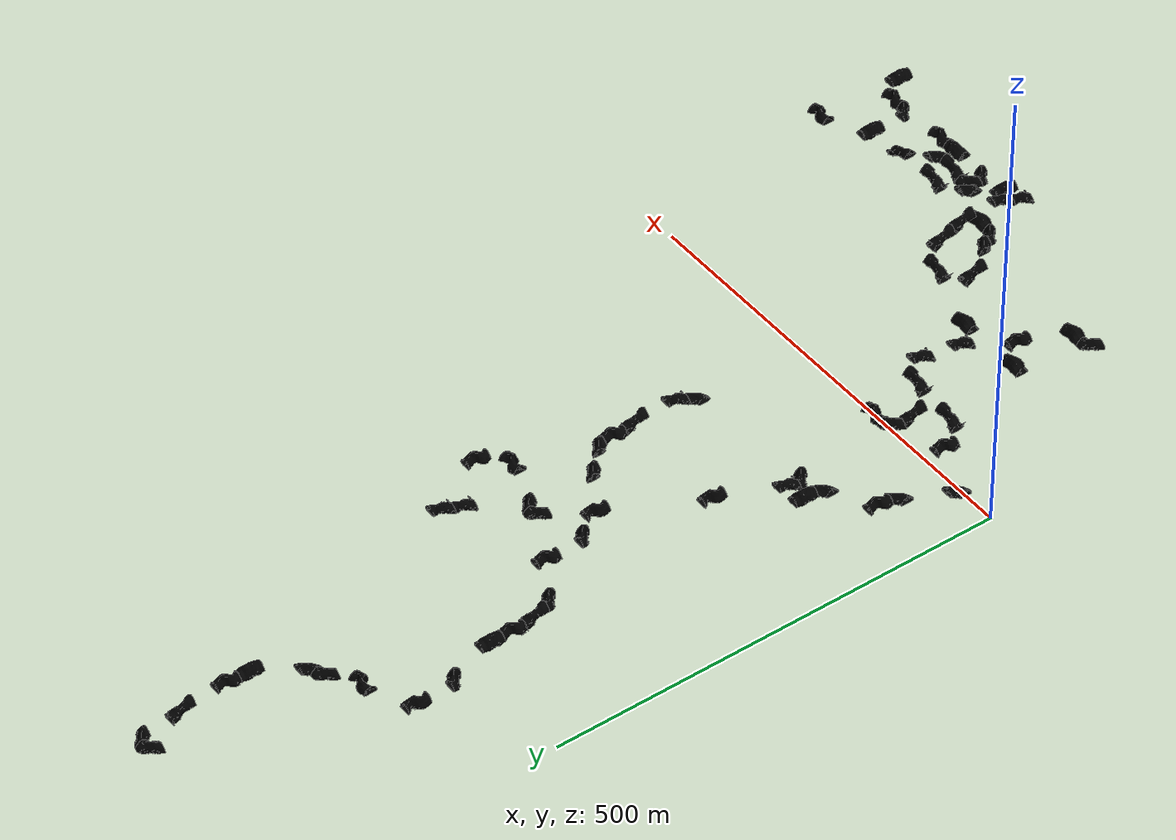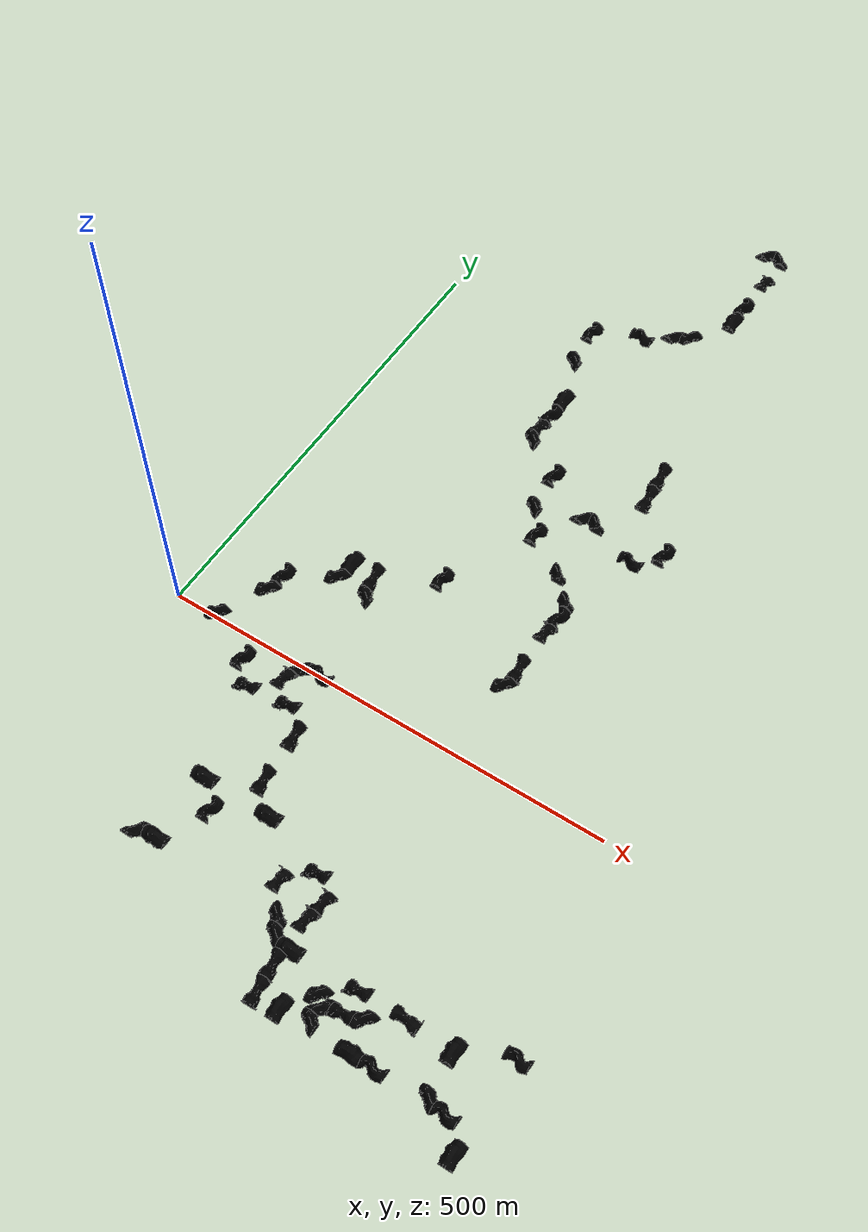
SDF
<sdf version="1.6">
 <world name="cave_circuit_01">
  <physics name="1ms" type="ode">
   <max_step_size>0.004</max_step_size>
   <real_time_factor>1.0</real_time_factor>
  </physics>
  <scene>
   <ambient>0.1 0.1 0.1 1.0</ambient>
   <background>0 0 0 1.0</background>
   <grid>false</grid>
   <origin_visual>false</origin_visual>
  </scene>
  <atmosphere type="adiabatic">
   <temperature>288</temperature>
   <temperature_gradient>0.3</temperature_gradient>
  </atmosphere>
  <model name="robot_diferencial">
   <link name="chassis">
    <pose relative_to="__model__">0.5 0 0.4 0 0 0</pose>
    <inertial>
     <mass>1.14395</mass>
     <inertia>
      <ixx>0.095329</ixx>
      <ixy>0</ixy>
      <ixz>0</ixz>
      <iyy>0.381317</iyy>
      <iyz>0</iyz>
      <izz>0.476646</izz>
     </inertia>
    </inertial>
    <visual name="visual">
     <geometry><box><size>2.0 1.0 0.5</size></box></geometry>
     <material>
      <ambient>0.0 0.0 1.0 1</ambient>
      <diffuse>0.0 0.0 1.0 1</diffuse>
      <specular>0.0 0.0 1.0 1</specular>
     </material>
    </visual>
    <collision name="collision"><geometry><box><size>2.0 1.0 0.5</size></box></geometry></collision>
   </link>
   <link name="left_wheel">
    <pose relative_to="chassis">-0.5 0.6 0 -1.5707 0 0</pose>
    <inertial>
     <mass>1</mass>
     <inertia><ixx>0.043333</ixx><ixy>0</ixy><ixz>0</ixz><iyy>0.043333</iyy><iyz>0</iyz><izz>0.08</izz></inertia>
    </inertial>
    <visual name="visual">
     <geometry><cylinder><radius>0.4</radius><length>0.2</length></cylinder></geometry>
     <material>
      <ambient>1.0 0.0 0.0 1</ambient>
      <diffuse>1.0 0.0 0.0 1</diffuse>
      <specular>1.0 0.0 0.0 1</specular>
     </material>
    </visual>
    <collision name="collision">
     <geometry><cylinder><radius>0.4</radius><length>0.2</length></cylinder></geometry>
    </collision>
   </link>
   <link name="right_wheel">
    <pose relative_to="chassis">-0.5 -0.6 0 -1.5707 0 0</pose>
    <inertial>
     <mass>1</mass>
     <inertia><ixx>0.043333</ixx><ixy>0</ixy><ixz>0</ixz><iyy>0.043333</iyy><iyz>0</iyz><izz>0.08</izz></inertia>
    </inertial>
    <visual name="visual">
     <geometry><cylinder><radius>0.4</radius><length>0.2</length></cylinder></geometry>
     <material>
      <ambient>1.0 0.0 0.0 1</ambient>
      <diffuse>1.0 0.0 0.0 1</diffuse>
      <specular>1.0 0.0 0.0 1</specular>
     </material>
    </visual>
    <collision name="collision">
     <geometry><cylinder><radius>0.4</radius><length>0.2</length></cylinder></geometry>
    </collision>
   </link>
   <link name="caster">
    <pose relative_to="chassis">0.8 0 -0.2 0 0 0</pose>
    <inertial>
     <mass>1</mass>
     <inertia><ixx>0.016</ixx><ixy>0</ixy><ixz>0</ixz><iyy>0.016</iyy><iyz>0</iyz><izz>0.016</izz></inertia>
    </inertial>
    <visual name="visual">
     <geometry><sphere><radius>0.2</radius></sphere></geometry>
     <material>
      <ambient>0.0 1 0.0 1</ambient>
      <diffuse>0.0 1 0.0 1</diffuse>
      <specular>0.0 1 0.0 1</specular>
     </material>
    </visual>
    <collision name="collision"><geometry><sphere><radius>0.2</radius></sphere></geometry></collision>
   </link>
   <joint name="left_wheel_joint" type="revolute">
    <pose relative_to="left_wheel"/>
    <parent>chassis</parent>
    <child>left_wheel</child>
    <axis><xyz expressed_in="__model__">0 1 0</xyz></axis>
   </joint>
   <joint name="right_wheel_joint" type="revolute">
    <pose relative_to="right_wheel"/>
    <parent>chassis</parent>
    <child>right_wheel</child>
    <axis><xyz expressed_in="__model__">0 1 0</xyz></axis>
   </joint>
   <joint name="caster_wheel" type="ball"><parent>chassis</parent><child>caster</child></joint>
   <plugin filename="gz-sim-diff-drive-system" name="gz::sim::systems::DiffDrive">
    <left_joint>left_wheel_joint</left_joint>
    <right_joint>right_wheel_joint</right_joint>
    <wheel_separation>1.2</wheel_separation>
    <wheel_radius>0.4</wheel_radius>
    <odom_publish_frequency>1</odom_publish_frequency>
    <topic>/turtle1/cmd_vel</topic>
   </plugin>
  </model>
  <include>
   <static>true</static>
   <name>tile_3</name>
   <pose>75 50 0 0 0 -0</pose>
   <uri>https://fuel.ignitionrobotics.org/1.0/OpenRobotics/models/Cave Corner 02 Lights Type B</uri>
  </include>
  <include>
   <static>true</static>
   <name>tile_5</name>
   <pose>125 125 0 0 -0 0</pose>
   <uri>https://fuel.ignitionrobotics.org/1.0/OpenRobotics/models/Cave Straight 04 Lights Type B</uri>
  </include>
  <include>
   <static>true</static>
   <name>tile_7</name>
   <pose>125 100 0 0 0 -0</pose>
   <uri>https://fuel.ignitionrobotics.org/1.0/OpenRobotics/models/Cave Corner 02 Lights Type B</uri>
  </include>
  <include>
   <static>true</static>
   <name>tile_8</name>
   <pose>75 75 0 0 -0 0</pose>
   <uri>https://fuel.ignitionrobotics.org/1.0/OpenRobotics/models/Cave Straight 03 Type B</uri>
  </include>
  <include>
   <static>true</static>
   <name>tile_9</name>
   <pose>50 0 0 0 0 -0</pose>
   <uri>https://fuel.ignitionrobotics.org/1.0/OpenRobotics/models/Cave Corner 02 Lights Type B</uri>
  </include>
  <include>
   <static>true</static>
   <name>tile_10</name>
   <pose>150 -25 0 0 0 -0</pose>
   <uri>https://fuel.ignitionrobotics.org/1.0/OpenRobotics/models/Cave Elevation Lights Type B</uri>
  </include>
  <include>
   <static>true</static>
   <name>tile_17</name>
   <pose>175 0 0 0 0 -1.5708</pose>
   <uri>https://fuel.ignitionrobotics.org/1.0/OpenRobotics/models/Cave Straight 03 Type B</uri>
  </include>
  <include>
   <static>true</static>
   <name>tile_18</name>
   <pose>100 -25 0 0 0 -0</pose>
   <uri>https://fuel.ignitionrobotics.org/1.0/OpenRobotics/models/Cave Straight 03 Type B</uri>
  </include>
  <include>
   <static>true</static>
   <name>tile_22</name>
   <pose>150 0 0 0 -0 3.14159</pose>
   <uri>https://fuel.ignitionrobotics.org/1.0/OpenRobotics/models/Cave Corner 02 Lights Type B</uri>
  </include>
  <include>
   <static>true</static>
   <name>tile_24</name>
   <pose>325 100 -30 0 -0 0</pose>
   <uri>https://fuel.ignitionrobotics.org/1.0/OpenRobotics/models/Cave Corner 02 Lights Type B</uri>
  </include>
  <include>
   <static>true</static>
   <name>tile_25</name>
   <pose>300 250 -30 0 -0 1.5708</pose>
   <uri>https://fuel.ignitionrobotics.org/1.0/OpenRobotics/models/Cave Corner 02 Lights Type B</uri>
  </include>
  <include>
   <static>true</static>
   <name>tile_26</name>
   <pose>325 225 -30 0 -0 1.5708</pose>
   <uri>https://fuel.ignitionrobotics.org/1.0/OpenRobotics/models/Cave Corner 02 Lights Type B</uri>
  </include>
  <include>
   <static>true</static>
   <name>tile_28</name>
   <pose>325 200 -30 0 0 -0</pose>
   <uri>https://fuel.ignitionrobotics.org/1.0/OpenRobotics/models/Cave Straight 03 Type B</uri>
  </include>
  <include>
   <static>true</static>
   <name>tile_29</name>
   <pose>325 175 -30 0 0 -0</pose>
   <uri>https://fuel.ignitionrobotics.org/1.0/OpenRobotics/models/Cave Elevation Lights Type B</uri>
  </include>
  <include>
   <static>true</static>
   <name>tile_30</name>
   <pose>325 125 -30 0 -0 3.14159</pose>
   <uri>https://fuel.ignitionrobotics.org/1.0/OpenRobotics/models/Cave Elevation Lights Type B</uri>
  </include>
  <include>
   <static>true</static>
   <name>tile_38</name>
   <pose>200 175 -30 0 0 -3.14159</pose>
   <uri>https://fuel.ignitionrobotics.org/1.0/OpenRobotics/models/Cave Straight 03 Type B</uri>
  </include>
  <include>
   <static>true</static>
   <name>tile_40</name>
   <pose>125 -50 0 0 -0 1.5708</pose>
   <uri>https://fuel.ignitionrobotics.org/1.0/OpenRobotics/models/Cave Elevation Lights Type B</uri>
  </include>
  <include>
   <static>true</static>
   <name>tile_41</name>
   <pose>175 -50 10 0 -0 1.5708</pose>
   <uri>https://fuel.ignitionrobotics.org/1.0/OpenRobotics/models/Cave Elevation Lights Type B</uri>
  </include>
  <include>
   <static>true</static>
   <name>tile_46</name>
   <pose>150 125 -10 0 -0 3.14159</pose>
   <uri>https://fuel.ignitionrobotics.org/1.0/OpenRobotics/models/Cave Elevation Lights Type B</uri>
  </include>
  <include>
   <static>true</static>
   <name>tile_47</name>
   <pose>150 100 -10 0 0 -1.5708</pose>
   <uri>https://fuel.ignitionrobotics.org/1.0/OpenRobotics/models/Cave Corner 02 Lights Type B</uri>
  </include>
  <include>
   <static>true</static>
   <name>tile_51</name>
   <pose>250 275 -30 0 -0 3.14159</pose>
   <uri>https://fuel.ignitionrobotics.org/1.0/OpenRobotics/models/Cave Straight 03 Type B</uri>
  </include>
  <include>
   <static>true</static>
   <name>tile_53</name>
   <pose>225 300 -30 0 0 -1.5708</pose>
   <uri>https://fuel.ignitionrobotics.org/1.0/OpenRobotics/models/Cave Corner 02 Lights Type B</uri>
  </include>
  <include>
   <static>true</static>
   <name>tile_54</name>
   <pose>275 325 -30 0 0 -3.14159</pose>
   <uri>https://fuel.ignitionrobotics.org/1.0/OpenRobotics/models/Cave Corner 02 Lights Type B</uri>
  </include>
  <include>
   <static>true</static>
   <name>tile_55</name>
   <pose>300 325 -30 0 -0 1.5708</pose>
   <uri>https://fuel.ignitionrobotics.org/1.0/OpenRobotics/models/Cave Corner 02 Lights Type B</uri>
  </include>
  <include>
   <static>true</static>
   <name>tile_58</name>
   <pose>350 300 -30 0 0 -1.5708</pose>
   <uri>https://fuel.ignitionrobotics.org/1.0/OpenRobotics/models/Cave Straight 03 Type B</uri>
  </include>
  <include>
   <static>true</static>
   <name>tile_63</name>
   <pose>375 325 -30 0 -0 0</pose>
   <uri>https://fuel.ignitionrobotics.org/1.0/OpenRobotics/models/Cave Straight 03 Type B</uri>
  </include>
  <include>
   <static>true</static>
   <name>tile_65</name>
   <pose>325 400 -20 0 -0 3.14159</pose>
   <uri>https://fuel.ignitionrobotics.org/1.0/OpenRobotics/models/Cave Elevation Type B</uri>
  </include>
  <include>
   <static>true</static>
   <name>tile_66</name>
   <pose>325 375 -30 0 -0 3.14159</pose>
   <uri>https://fuel.ignitionrobotics.org/1.0/OpenRobotics/models/Cave Elevation Type B</uri>
  </include>
  <include>
   <static>true</static>
   <name>tile_69</name>
   <pose>225 350 -30 0 -0 0</pose>
   <uri>https://fuel.ignitionrobotics.org/1.0/OpenRobotics/models/Cave Straight 03 Type B</uri>
  </include>
  <include>
   <static>true</static>
   <name>tile_72</name>
   <pose>175 375 -30 0 0 -1.5708</pose>
   <uri>https://fuel.ignitionrobotics.org/1.0/OpenRobotics/models/Cave Corner 02 Type B</uri>
  </include>
  <include>
   <static>true</static>
   <name>tile_73</name>
   <pose>175 400 -40 0 0 -0</pose>
   <uri>https://fuel.ignitionrobotics.org/1.0/OpenRobotics/models/Cave Elevation Type B</uri>
  </include>
  <include>
   <static>true</static>
   <name>tile_74</name>
   <pose>175 425 -40 0 0 -0</pose>
   <uri>https://fuel.ignitionrobotics.org/1.0/OpenRobotics/models/Cave Straight 03 Type B</uri>
  </include>
  <include>
   <static>true</static>
   <name>tile_77</name>
   <pose>150 500 -40 0 0 -1.5708</pose>
   <uri>https://fuel.ignitionrobotics.org/1.0/OpenRobotics/models/Cave Corner 02 Type B</uri>
  </include>
  <include>
   <static>true</static>
   <name>tile_79</name>
   <pose>150 550 -40 0 -0 3.14159</pose>
   <uri>https://fuel.ignitionrobotics.org/1.0/OpenRobotics/models/Cave Straight 03 Type B</uri>
  </include>
  <include>
   <static>true</static>
   <name>tile_80</name>
   <pose>175 450 -40 0 -0 0</pose>
   <uri>https://fuel.ignitionrobotics.org/1.0/OpenRobotics/models/Cave Straight 04 Type B</uri>
  </include>
  <include>
   <static>true</static>
   <name>tile_83</name>
   <pose>200 575 -40 0 -0 1.5708</pose>
   <uri>https://fuel.ignitionrobotics.org/1.0/OpenRobotics/models/Cave Straight 03 Type B</uri>
  </include>
  <include>
   <static>true</static>
   <name>tile_85</name>
   <pose>225 600 -40 0 0 -3.14159</pose>
   <uri>https://fuel.ignitionrobotics.org/1.0/OpenRobotics/models/Cave Corner 02 Type B</uri>
  </include>
  <include>
   <static>true</static>
   <name>tile_86</name>
   <pose>250 600 -40 0 -0 0</pose>
   <uri>https://fuel.ignitionrobotics.org/1.0/OpenRobotics/models/Cave Corner 02 Type B</uri>
  </include>
  <include>
   <static>true</static>
   <name>tile_89</name>
   <pose>275 725 -50 0 0 -0</pose>
   <uri>https://fuel.ignitionrobotics.org/1.0/OpenRobotics/models/Cave Elevation Type B</uri>
  </include>
  <include>
   <static>true</static>
   <name>tile_91</name>
   <pose>275 675 -40 0 0 -0</pose>
   <uri>https://fuel.ignitionrobotics.org/1.0/OpenRobotics/models/Cave Straight 03 Type B</uri>
  </include>
  <include>
   <static>true</static>
   <name>tile_92</name>
   <pose>275 650 -40 0 -0 0</pose>
   <uri>https://fuel.ignitionrobotics.org/1.0/OpenRobotics/models/Cave Straight 04 Type B</uri>
  </include>
  <include>
   <static>true</static>
   <name>tile_94</name>
   <pose>250 775 -50 0 -0 3.14159</pose>
   <uri>https://fuel.ignitionrobotics.org/1.0/OpenRobotics/models/Cave Corner 02 Type B</uri>
  </include>
  <include>
   <static>true</static>
   <name>tile_95</name>
   <pose>275 775 -50 0 -0 1.5708</pose>
   <uri>https://fuel.ignitionrobotics.org/1.0/OpenRobotics/models/Cave Corner 02 Type B</uri>
  </include>
  <include>
   <static>true</static>
   <name>tile_101</name>
   <pose>225 -150 0 0 -0 1.5708</pose>
   <uri>https://fuel.ignitionrobotics.org/1.0/OpenRobotics/models/Cave Straight 04 Type B</uri>
  </include>
  <include>
   <static>true</static>
   <name>tile_104</name>
   <pose>300 -175 0 0 -0 1.5708</pose>
   <uri>https://fuel.ignitionrobotics.org/1.0/OpenRobotics/models/Cave Elevation Type B</uri>
  </include>
  <include>
   <static>true</static>
   <name>tile_105</name>
   <pose>275 -200 0 0 -0 0</pose>
   <uri>https://fuel.ignitionrobotics.org/1.0/OpenRobotics/models/Cave Elevation Type B</uri>
  </include>
  <include>
   <static>true</static>
   <name>tile_107</name>
   <pose>300 -225 10 0 -0 1.5708</pose>
   <uri>https://fuel.ignitionrobotics.org/1.0/OpenRobotics/models/Cave Corner 02 Type B</uri>
  </include>
  <include>
   <static>true</static>
   <name>tile_110</name>
   <pose>175 -175 0 0 -0 0</pose>
   <uri>https://fuel.ignitionrobotics.org/1.0/OpenRobotics/models/Cave Straight 03 Type B</uri>
  </include>
  <include>
   <static>true</static>
   <name>tile_112</name>
   <pose>150 -150 0 0 -0 1.5708</pose>
   <uri>https://fuel.ignitionrobotics.org/1.0/OpenRobotics/models/Cave Straight 04 Type B</uri>
  </include>
  <include>
   <static>true</static>
   <name>tile_115</name>
   <pose>325 -250 10 0 -0 1.5708</pose>
   <uri>https://fuel.ignitionrobotics.org/1.0/OpenRobotics/models/Cave Straight 04 Type B</uri>
  </include>
  <include>
   <static>true</static>
   <name>tile_116</name>
   <pose>325 -200 10 0 0 -0</pose>
   <uri>https://fuel.ignitionrobotics.org/1.0/OpenRobotics/models/Cave Elevation Type B</uri>
  </include>
  <include>
   <static>true</static>
   <name>tile_117</name>
   <pose>325 -225 20 0 0 -0</pose>
   <uri>https://fuel.ignitionrobotics.org/1.0/OpenRobotics/models/Cave Elevation Type B</uri>
  </include>
  <include>
   <static>true</static>
   <name>tile_118</name>
   <pose>300 -250 10 0 0 -1.5708</pose>
   <uri>https://fuel.ignitionrobotics.org/1.0/OpenRobotics/models/Cave Corner 02 Type B</uri>
  </include>
  <include>
   <static>true</static>
   <name>tile_125</name>
   <pose>425 -275 20 0 -0 0</pose>
   <uri>https://fuel.ignitionrobotics.org/1.0/OpenRobotics/models/Cave Corner 02 Type B</uri>
  </include>
  <include>
   <static>true</static>
   <name>tile_126</name>
   <pose>400 -250 10 0 -0 1.5708</pose>
   <uri>https://fuel.ignitionrobotics.org/1.0/OpenRobotics/models/Cave Elevation Type B</uri>
  </include>
  <include>
   <static>true</static>
   <name>tile_127</name>
   <pose>400 -275 10 0 -0 1.5708</pose>
   <uri>https://fuel.ignitionrobotics.org/1.0/OpenRobotics/models/Cave Elevation Type B</uri>
  </include>
  <include>
   <static>true</static>
   <name>tile_128</name>
   <pose>375 -275 10 0 -0 0</pose>
   <uri>https://fuel.ignitionrobotics.org/1.0/OpenRobotics/models/Cave Corner 02 Type B</uri>
  </include>
  <include>
   <static>true</static>
   <name>tile_129</name>
   <pose>375 -275 10 0 -0 3.14159</pose>
   <uri>https://fuel.ignitionrobotics.org/1.0/OpenRobotics/models/Cave Corner 02 Type B</uri>
  </include>
  <include>
   <static>true</static>
   <name>tile_131</name>
   <pose>450 -250 10 0 -0 -1.5708</pose>
   <uri>https://fuel.ignitionrobotics.org/1.0/OpenRobotics/models/Cave Elevation Type B</uri>
  </include>
  <include>
   <static>true</static>
   <name>tile_132</name>
   <pose>350 -300 10 0 -0 0</pose>
   <uri>https://fuel.ignitionrobotics.org/1.0/OpenRobotics/models/Cave Straight 04 Type B</uri>
  </include>
  <include>
   <static>true</static>
   <name>tile_133</name>
   <pose>375 -300 10 0 0 -1.5708</pose>
   <uri>https://fuel.ignitionrobotics.org/1.0/OpenRobotics/models/Cave Corner 02 Type B</uri>
  </include>
  <include>
   <static>true</static>
   <name>tile_136</name>
   <pose>450 -300 10 0 0 -1.5708</pose>
   <uri>https://fuel.ignitionrobotics.org/1.0/OpenRobotics/models/Cave Straight 03 Type B</uri>
  </include>
  <include>
   <static>true</static>
   <name>tile_138</name>
   <pose>425 -300 10 0 0 -1.5708</pose>
   <uri>https://fuel.ignitionrobotics.org/1.0/OpenRobotics/models/Cave Straight 04 Type B</uri>
  </include>
  <include>
   <static>true</static>
   <name>tile_141</name>
   <pose>150 -225 0 0 -0 1.5708</pose>
   <uri>https://fuel.ignitionrobotics.org/1.0/OpenRobotics/models/Cave Straight 04 Type B</uri>
  </include>
  <include>
   <static>true</static>
   <name>tile_142</name>
   <pose>125 -225 0 0 -0 3.14159</pose>
   <uri>https://fuel.ignitionrobotics.org/1.0/OpenRobotics/models/Cave Corner 02 Type B</uri>
  </include>
  <include>
   <static>true</static>
   <name>tile_147</name>
   <pose>500 -300 10 0 0 -1.5708</pose>
   <uri>https://fuel.ignitionrobotics.org/1.0/OpenRobotics/models/Cave Corner 02 Type B</uri>
  </include>
  <include>
   <static>true</static>
   <name>tile_148</name>
   <pose>525 -300 10 0 0 -1.5708</pose>
   <uri>https://fuel.ignitionrobotics.org/1.0/OpenRobotics/models/Cave Straight 03 Type B</uri>
  </include>
  <include>
   <static>true</static>
   <name>tile_149</name>
   <pose>500 -250 10 0 -0 0</pose>
   <uri>https://fuel.ignitionrobotics.org/1.0/OpenRobotics/models/Cave Straight 04 Type B</uri>
  </include>
  <include>
   <static>true</static>
   <name>tile_150</name>
   <pose>550 -325 10 0 -0 0</pose>
   <uri>https://fuel.ignitionrobotics.org/1.0/OpenRobotics/models/Cave Straight 04 Type B</uri>
  </include>
  <include>
   <static>true</static>
   <name>tile_153</name>
   <pose>550 -225 10 0 -0 1.5708</pose>
   <uri>https://fuel.ignitionrobotics.org/1.0/OpenRobotics/models/Cave Straight 03 Type B</uri>
  </include>
  <include>
   <static>true</static>
   <name>tile_154</name>
   <pose>200 -125 0 0 0 -3.14159</pose>
   <uri>https://fuel.ignitionrobotics.org/1.0/OpenRobotics/models/Cave Elevation Type B</uri>
  </include>
  <include>
   <static>true</static>
   <name>tile_155</name>
   <pose>200 -75 10 0 0 -3.14159</pose>
   <uri>https://fuel.ignitionrobotics.org/1.0/OpenRobotics/models/Cave Elevation Type B</uri>
  </include>
  <include>
   <static>true</static>
   <name>tile_156</name>
   <pose>325 -275 20 0 -0 3.14159</pose>
   <uri>https://fuel.ignitionrobotics.org/1.0/OpenRobotics/models/Cave Elevation Type B</uri>
  </include>
  <include>
   <static>true</static>
   <name>tile_157</name>
   <pose>325 -300 10 0 -0 3.14159</pose>
   <uri>https://fuel.ignitionrobotics.org/1.0/OpenRobotics/models/Cave Elevation Type B</uri>
  </include>
 </world>
</sdf>

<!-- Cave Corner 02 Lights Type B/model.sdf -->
<sdf version="1.6">
  <model name="Cave Corner 02 Lights Type B">
    <include>
      <name>cave_corner_02</name>
      <uri>model://Cave Corner 02 Type B</uri>
    </include>
    <static>true</static>
    <link name="lights">
      <light name="spot_light1" type="spot">
        <pose>-2 6.0 3.5 0 0 0</pose>
        <diffuse>0 0 0 1</diffuse>
        <specular>0 0 0 1</specular>
        <attenuation>
          <range>20</range>
          <linear>0.2</linear>
          <constant>0.5</constant>
          <quadratic>0.02</quadratic>
        </attenuation>
        <spot>
          <inner_angle>2.0</inner_angle>
          <outer_angle>3.1</outer_angle>
          <falloff>1.0</falloff>
        </spot>
        <cast_shadows>false</cast_shadows>
      </light>

      <light name="spot_light2" type="spot">
        <pose>-6.5 -.25 4.5 0 0 0</pose>
        <diffuse>0 0 0 1</diffuse>
        <specular>0 0 0 1</specular>
        <attenuation>
          <range>20</range>
          <linear>0.2</linear>
          <constant>0.5</constant>
          <quadratic>0.02</quadratic>
        </attenuation>
        <spot>
          <inner_angle>2.0</inner_angle>
          <outer_angle>3.1</outer_angle>
          <falloff>1.0</falloff>
        </spot>
        <cast_shadows>false</cast_shadows>
      </light>
    </link>
  </model>
</sdf>

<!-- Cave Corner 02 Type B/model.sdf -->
<sdf version="1.6">
  <model name="Cave Corner 02 Type B">
    <static>true</static>
    <link name="base_link">
      <collision name="collision">
        <pose>0 0 0 0 0 0</pose>
        <geometry>
          <mesh>
            <uri>model://cave_corner_02/meshes/cavecorner02.dae</uri>
            <scale>1.005 1.005 1.0</scale>
          </mesh>
        </geometry>
      </collision>
      <visual name="CaveWall_visual">
        <geometry>
          <mesh>
            <uri>model://cave_corner_02/meshes/cavecorner02.dae</uri>
            <submesh>
              <name>CaveWall</name>
              <center>false</center>
            </submesh>
            <scale>1.005 1.005 1.0</scale>
          </mesh>
        </geometry>
        <material>
          <diffuse>0 0 0 1</diffuse>
          <specular>0 0 0 1</specular>
          <pbr>
            <metal>
              <albedo_map>model://cave_corner_02/materials/textures/CaveWall_Albedo.png</albedo_map>
              <normal_map>model://cave_corner_02/materials/textures/CaveWall_Normal.png</normal_map>
              <roughness_map>model://cave_corner_02/materials/textures/CaveWall_Roughness.png</roughness_map>
            </metal>
          </pbr>

          <script>
            <uri>model://cave_corner_02/materials/scripts/</uri>
            <uri>model://cave_corner_02/materials/textures/</uri>
            <name>CaveTile/CaveWall_Diffuse</name>
          </script>
        </material>
      </visual>
      <visual name="StriatedRock_visual">
        <geometry>
          <mesh>
            <uri>model://cave_corner_02/meshes/cavecorner02.dae</uri>
            <submesh>
              <name>StriatedRock</name>
              <center>false</center>
            </submesh>
            <scale>1.005 1.005 1.0</scale>
          </mesh>
        </geometry>
        <material>
          <diffuse>0 0 0 1</diffuse>
          <specular>0 0 0 1</specular>
          <pbr>
            <metal>
              <albedo_map>model://cave_corner_02/materials/textures/StriatedRock_Albedo.png</albedo_map>
              <normal_map>model://cave_corner_02/materials/textures/StriatedRock_Normal.png</normal_map>
              <roughness_map>model://cave_corner_02/materials/textures/StriatedRock_Roughness.png</roughness_map>
            </metal>
          </pbr>

          <script>
            <uri>model://cave_corner_02/materials/scripts/</uri>
            <uri>model://cave_corner_02/materials/textures/</uri>
            <name>CaveTile/StriatedRock_Diffuse</name>
          </script>
        </material>
      </visual>
      <visual name="RockPile_visual">
        <geometry>
          <mesh>
            <uri>model://cave_corner_02/meshes/cavecorner02.dae</uri>
            <submesh>
              <name>RockPile</name>
              <center>false</center>
            </submesh>
            <scale>1.005 1.005 1.0</scale>
          </mesh>
        </geometry>
        <material>
          <diffuse>0 0 0 1</diffuse>
          <specular>0 0 0 1</specular>
          <pbr>
            <metal>
              <albedo_map>model://cave_corner_02/materials/textures/RockPile_Albedo.png</albedo_map>
              <normal_map>model://cave_corner_02/materials/textures/RockPile_Normal.png</normal_map>
              <roughness_map>model://cave_corner_02/materials/textures/RockPile_Roughness.png</roughness_map>
            </metal>
          </pbr>

          <script>
            <uri>model://cave_corner_02/materials/scripts/</uri>
            <uri>model://cave_corner_02/materials/textures/</uri>
            <name>CaveTile/RockPile_Diffuse</name>
          </script>
        </material>
      </visual>
    </link>
  </model>
</sdf>

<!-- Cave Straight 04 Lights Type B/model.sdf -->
<sdf version="1.6">
  <model name="Cave Straight 04 Lights Type B">
    <include>
      <name>cave_straight_04</name>
      <uri>model://Cave Straight 04 Type B</uri>
    </include>
    <static>true</static>
    <link name="lights">
      <light name="spot_light1" type="spot">
        <pose>0 8 8.0 0 0 0</pose>
        <diffuse>0 0 0 1</diffuse>
        <specular>0 0 0 1</specular>
        <attenuation>
          <range>20</range>
          <linear>0.2</linear>
          <constant>0.3</constant>
          <quadratic>0.01</quadratic>
        </attenuation>
        <spot>
          <inner_angle>2.0</inner_angle>
          <outer_angle>3.1</outer_angle>
          <falloff>0.6</falloff>
        </spot>
        <cast_shadows>false</cast_shadows>
      </light>

      <light name="spot_light2" type="spot">
        <pose>0 -6.0 4.5 0 0 0</pose>
        <diffuse>0 0 0 1</diffuse>
        <specular>0 0 0 1</specular>
        <attenuation>
          <range>20</range>
          <linear>0.2</linear>
          <constant>0.3</constant>
          <quadratic>0.01</quadratic>
        </attenuation>
        <spot>
          <inner_angle>2.0</inner_angle>
          <outer_angle>3.1</outer_angle>
          <falloff>0.6</falloff>
        </spot>
        <cast_shadows>false</cast_shadows>
      </light>
    </link>
  </model>
</sdf>

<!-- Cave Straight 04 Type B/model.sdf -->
<sdf version="1.6">
  <model name="Cave Straight 04 Type B">
    <static>true</static>
    <link name="base_link">
      <collision name="collision">
        <pose>0 0 0 0 0 0</pose>
        <geometry>
          <mesh>
            <uri>model://Cave Straight 04 Type B/meshes/cavestraight04.dae</uri>
            <scale>1.0 1.0 1.0</scale>
          </mesh>
        </geometry>
      </collision>
      <visual name="StriatedRock_visual">
        <geometry>
          <mesh>
            <uri>model://Cave Straight 04 Type B/meshes/cavestraight04.dae</uri>
            <submesh>
              <name>StriatedRock</name>
              <center>false</center>
            </submesh>
          </mesh>
        </geometry>
        <material>
          <diffuse>0 0 0 1</diffuse>
          <specular>0 0 0 1</specular>
          <pbr>
            <metal>
              <albedo_map>model://Cave Straight 04 Type B/materials/textures/StriatedRock_Albedo.png</albedo_map>
              <normal_map>model://Cave Straight 04 Type B/materials/textures/StriatedRock_Normal.png</normal_map>
              <roughness_map>model://Cave Straight 04 Type B/materials/textures/StriatedRock_Roughness.png</roughness_map>
            </metal>
          </pbr>

          <script>
            <uri>model://Cave Straight 04 Type B/materials/scripts/</uri>
            <uri>model://Cave Straight 04 Type B/materials/textures/</uri>
            <name>CaveTile/StriatedRock_Diffuse</name>
          </script>
        </material>
      </visual>
      <visual name="RockPile_visual">
        <geometry>
          <mesh>
            <uri>model://Cave Straight 04 Type B/meshes/cavestraight04.dae</uri>
            <submesh>
              <name>RockPile</name>
              <center>false</center>
            </submesh>
          </mesh>
        </geometry>
        <material>
          <diffuse>0 0 0 1</diffuse>
          <specular>0 0 0 1</specular>
          <pbr>
            <metal>
              <albedo_map>model://Cave Straight 04 Type B/materials/textures/RockPile_Albedo.png</albedo_map>
              <normal_map>model://Cave Straight 04 Type B/materials/textures/RockPile_Normal.png</normal_map>
              <roughness_map>model://Cave Straight 04 Type B/materials/textures/RockPile_Roughness.png</roughness_map>
            </metal>
          </pbr>

          <script>
            <uri>model://Cave Straight 04 Type B/materials/scripts/</uri>
            <uri>model://Cave Straight 04 Type B/materials/textures/</uri>
            <name>CaveTile/RockPile_Diffuse</name>
          </script>
        </material>
      </visual>
      <visual name="CaveWall_visual">
        <geometry>
          <mesh>
            <uri>model://Cave Straight 04 Type B/meshes/cavestraight04.dae</uri>
            <submesh>
              <name>CaveWall</name>
              <center>false</center>
            </submesh>
          </mesh>
        </geometry>
        <material>
          <diffuse>0 0 0 1</diffuse>
          <specular>0 0 0 1</specular>
          <pbr>
            <metal>
              <albedo_map>model://Cave Straight 04 Type B/materials/textures/CaveWall_Albedo.png</albedo_map>
              <normal_map>model://Cave Straight 04 Type B/materials/textures/CaveWall_Normal.png</normal_map>
              <roughness_map>model://Cave Straight 04 Type B/materials/textures/CaveWall_Roughness.png</roughness_map>
            </metal>
          </pbr>

          <script>
            <uri>model://Cave Straight 04 Type B/materials/scripts/</uri>
            <uri>model://Cave Straight 04 Type B/materials/textures/</uri>
            <name>CaveTile/CaveWall_Diffuse</name>
          </script>
        </material>
      </visual>
    </link>
  </model>
</sdf>

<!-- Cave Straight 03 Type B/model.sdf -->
<sdf version="1.6">
  <model name="Cave Straight 03 Type B">
    <static>true</static>
    <link name="base_link">
      <collision name="collision">
        <pose>0 0 0 0 0 0</pose>
        <geometry>
          <mesh>
            <uri>model://Cave Straight 03 Type B/meshes/cavestraight03.dae</uri>
            <scale>1.005 1.005 1.0</scale>
          </mesh>
        </geometry>
      </collision>
      <visual name="StriatedRock_visual">
        <geometry>
          <mesh>
            <uri>model://Cave Straight 03 Type B/meshes/cavestraight03.dae</uri>
            <submesh>
              <name>StriatedRock</name>
              <center>false</center>
            </submesh>
            <scale>1.005 1.005 1.0</scale>
          </mesh>
        </geometry>
        <material>
          <diffuse>0 0 0 1</diffuse>
          <specular>0 0 0 1</specular>
          <pbr>
            <metal>
              <albedo_map>model://Cave Straight 03 Type B/materials/textures/StriatedRock_Albedo.png</albedo_map>
              <normal_map>model://Cave Straight 03 Type B/materials/textures/StriatedRock_Normal.png</normal_map>
              <roughness_map>model://Cave Straight 03 Type B/materials/textures/StriatedRock_Roughness.png</roughness_map>
            </metal>
          </pbr>

          <script>
            <uri>model://Cave Straight 03 Type B/materials/scripts/</uri>
            <uri>model://Cave Straight 03 Type B/materials/textures/</uri>
            <name>CaveTile/StriatedRock_Diffuse</name>
          </script>
        </material>
      </visual>
      <visual name="RockPile_visual">
        <geometry>
          <mesh>
            <uri>model://Cave Straight 03 Type B/meshes/cavestraight03.dae</uri>
            <submesh>
              <name>RockPile</name>
              <center>false</center>
            </submesh>
            <scale>1.005 1.005 1.0</scale>
          </mesh>
        </geometry>
        <material>
          <diffuse>0 0 0 1</diffuse>
          <specular>0 0 0 1</specular>
          <pbr>
            <metal>
              <albedo_map>model://Cave Straight 03 Type B/materials/textures/RockPile_Albedo.png</albedo_map>
              <normal_map>model://Cave Straight 03 Type B/materials/textures/RockPile_Normal.png</normal_map>
              <roughness_map>model://Cave Straight 03 Type B/materials/textures/RockPile_Roughness.png</roughness_map>
            </metal>
          </pbr>

          <script>
            <uri>model://Cave Straight 03 Type B/materials/scripts/</uri>
            <uri>model://Cave Straight 03 Type B/materials/textures/</uri>
            <name>CaveTile/RockPile_Diffuse</name>
          </script>
        </material>
      </visual>
      <visual name="CaveWall_visual">
        <geometry>
          <mesh>
            <uri>model://Cave Straight 03 Type B/meshes/cavestraight03.dae</uri>
            <submesh>
              <name>CaveWall</name>
              <center>false</center>
            </submesh>
            <scale>1.005 1.005 1.0</scale>
          </mesh>
        </geometry>
        <material>
          <diffuse>0 0 0 1</diffuse>
          <specular>0 0 0 1</specular>
          <pbr>
            <metal>
              <albedo_map>model://Cave Straight 03 Type B/materials/textures/CaveWall_Albedo.png</albedo_map>
              <normal_map>model://Cave Straight 03 Type B/materials/textures/CaveWall_Normal.png</normal_map>
              <roughness_map>model://Cave Straight 03 Type B/materials/textures/CaveWall_Roughness.png</roughness_map>
            </metal>
          </pbr>

          <script>
            <uri>model://Cave Straight 03 Type B/materials/scripts/</uri>
            <uri>model://Cave Straight 03 Type B/materials/textures/</uri>
            <name>CaveTile/CaveWall_Diffuse</name>
          </script>
        </material>
      </visual>
    </link>
  </model>
</sdf>

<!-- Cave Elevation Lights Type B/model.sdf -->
<sdf version="1.6">
  <model name="Cave Elevation Lights Type B">
    <static>true</static>
    <include>
      <name>cave_elevation</name>
      <uri>model://Cave Elevation Type B</uri>
    </include>

    <link name="light1">
      <light name="spot_light1" type="spot">
        <pose>0 -8 17.5 0 0 0</pose>
        <diffuse>0 0 0 1</diffuse>
        <specular>0 0 0 1</specular>
        <attenuation>
          <range>20</range>
          <linear>0.2</linear>
          <constant>1.0</constant>
          <quadratic>0.01</quadratic>
        </attenuation>
        <spot>
          <inner_angle>2.0</inner_angle>
          <outer_angle>3.1</outer_angle>
          <falloff>1.2</falloff>
        </spot>
        <cast_shadows>false</cast_shadows>
      </light>

      <light name="spot_light2" type="spot">
        <pose>0 2 13.5 0 0 0</pose>
        <diffuse>0 0 0 1</diffuse>
        <specular>0 0 0 1</specular>
        <attenuation>
          <range>20</range>
          <linear>0.2</linear>
          <constant>1.0</constant>
          <quadratic>0.01</quadratic>
        </attenuation>
        <spot>
          <inner_angle>2.0</inner_angle>
          <outer_angle>3.1</outer_angle>
          <falloff>1.2</falloff>
        </spot>
        <cast_shadows>false</cast_shadows>
      </light>

      <light name="spot_light3" type="spot">
        <pose>0 12 9 0 0 0</pose>
        <diffuse>0 0 0 1</diffuse>
        <specular>0 0 0 1</specular>
        <attenuation>
          <range>20</range>
          <linear>0.2</linear>
          <constant>1.0</constant>
          <quadratic>0.01</quadratic>
        </attenuation>
        <spot>
          <inner_angle>2.0</inner_angle>
          <outer_angle>3.1</outer_angle>
          <falloff>1.2</falloff>
        </spot>
        <cast_shadows>false</cast_shadows>
      </light>
    </link>
  </model>
</sdf>

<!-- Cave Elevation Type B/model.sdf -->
<sdf version="1.6">
  <model name="Cave Elevation Type B">
    <static>true</static>
    <link name="base_link">
      <collision name="collision">
        <pose>0 0 0 0 0 0</pose>
        <geometry>
          <mesh>
            <uri>model://Cave Elevation Type B/meshes/caveelevation.dae</uri>
            <scale>1.0 1.0 1.0</scale>
          </mesh>
        </geometry>
      </collision>
      <visual name="CaveWall_visual">
        <geometry>
          <mesh>
            <uri>model://Cave Elevation Type B/meshes/caveelevation.dae</uri>
            <submesh>
              <name>CaveWall</name>
              <center>false</center>
            </submesh>
          </mesh>
        </geometry>
        <material>
          <diffuse>0 0 0 1</diffuse>
          <specular>0 0 0 1</specular>
          <pbr>
            <metal>
              <albedo_map>model://Cave Elevation Type B/materials/textures/CaveWall_Albedo.png</albedo_map>
              <normal_map>model://Cave Elevation Type B/materials/textures/CaveWall_Normal.png</normal_map>
              <roughness_map>model://Cave Elevation Type B/materials/textures/CaveWall_Roughness.png</roughness_map>
            </metal>
          </pbr>

          <script>
            <uri>model://Cave Elevation Type B/materials/scripts/</uri>
            <uri>model://Cave Elevation Type B/materials/textures/</uri>
            <name>CaveTile/CaveWall_Diffuse</name>
          </script>
        </material>
      </visual>
      <visual name="RockPile_visual">
        <geometry>
          <mesh>
            <uri>model://Cave Elevation Type B/meshes/caveelevation.dae</uri>
            <submesh>
              <name>RockPile</name>
              <center>false</center>
            </submesh>
          </mesh>
        </geometry>
        <material>
          <diffuse>0 0 0 1</diffuse>
          <specular>0 0 0 1</specular>
          <pbr>
            <metal>
              <albedo_map>model://Cave Elevation Type B/materials/textures/RockPile_Albedo.png</albedo_map>
              <normal_map>model://Cave Elevation Type B/materials/textures/RockPile_Normal.png</normal_map>
              <roughness_map>model://Cave Elevation Type B/materials/textures/RockPile_Roughness.png</roughness_map>
            </metal>
          </pbr>

          <script>
            <uri>model://Cave Elevation Type B/materials/scripts/</uri>
            <uri>model://Cave Elevation Type B/materials/textures/</uri>
            <name>CaveTile/RockPile_Diffuse</name>
          </script>
        </material>
      </visual>
      <visual name="StriatedRock_visual">
        <geometry>
          <mesh>
            <uri>model://Cave Elevation Type B/meshes/caveelevation.dae</uri>
            <submesh>
              <name>StriatedRock</name>
              <center>false</center>
            </submesh>
          </mesh>
        </geometry>
        <material>
          <diffuse>0 0 0 1</diffuse>
          <specular>0 0 0 1</specular>
          <pbr>
            <metal>
              <albedo_map>model://Cave Elevation Type B/materials/textures/StriatedRock_Albedo.png</albedo_map>
              <normal_map>model://Cave Elevation Type B/materials/textures/StriatedRock_Normal.png</normal_map>
              <roughness_map>model://Cave Elevation Type B/materials/textures/StriatedRock_Roughness.png</roughness_map>
            </metal>
          </pbr>

          <script>
            <uri>model://Cave Elevation Type B/materials/scripts/</uri>
            <uri>model://Cave Elevation Type B/materials/textures/</uri>
            <name>CaveTile/StriatedRock_Diffuse</name>
          </script>
        </material>
      </visual>
    </link>

    <plugin filename="libignition-gazebo-performer-detector-system.so" name="ignition::gazebo::systems::PerformerDetector">
      <topic>/subt_performer_detector</topic>
      <pose>0 0 10 0 0 0</pose>
      <geometry>
        <box>
          <size>20 30 20</size>
        </box>
      </geometry>
      <header_data>
        <key>type</key>
        <value>elevation</value>
      </header_data>
    </plugin>
  </model>
</sdf>
